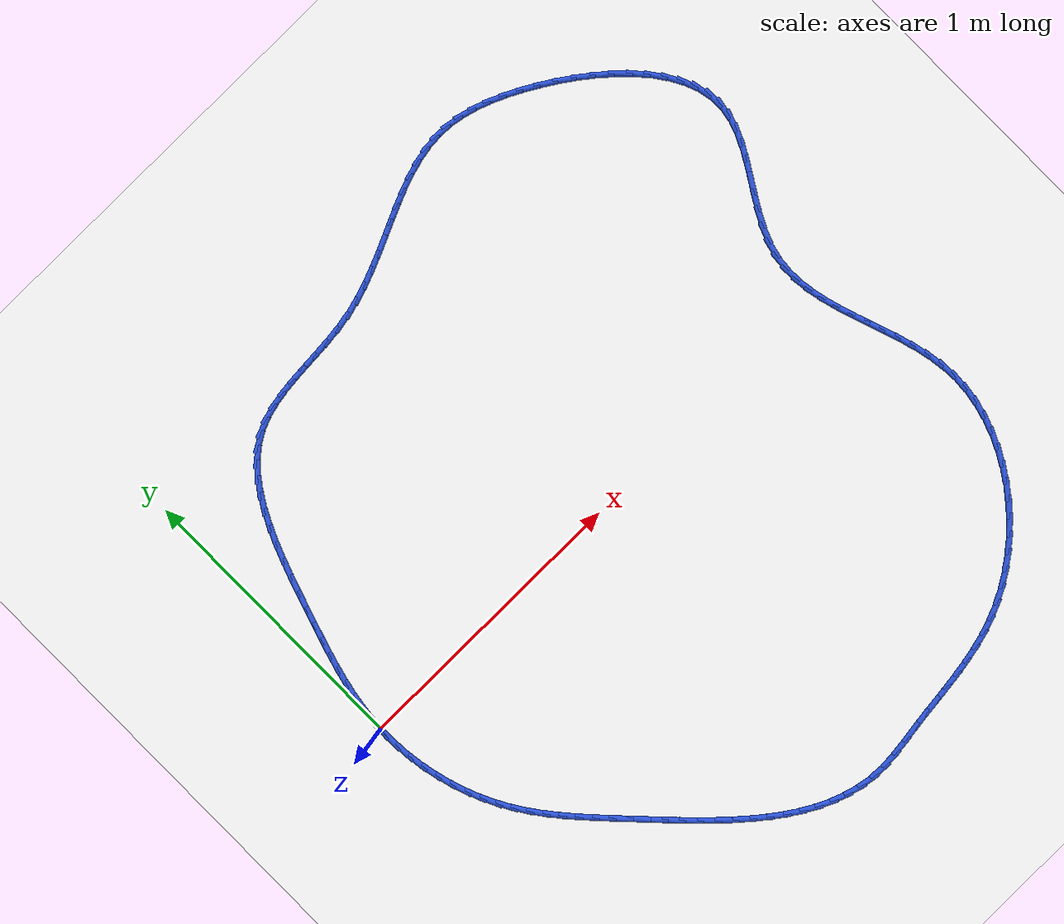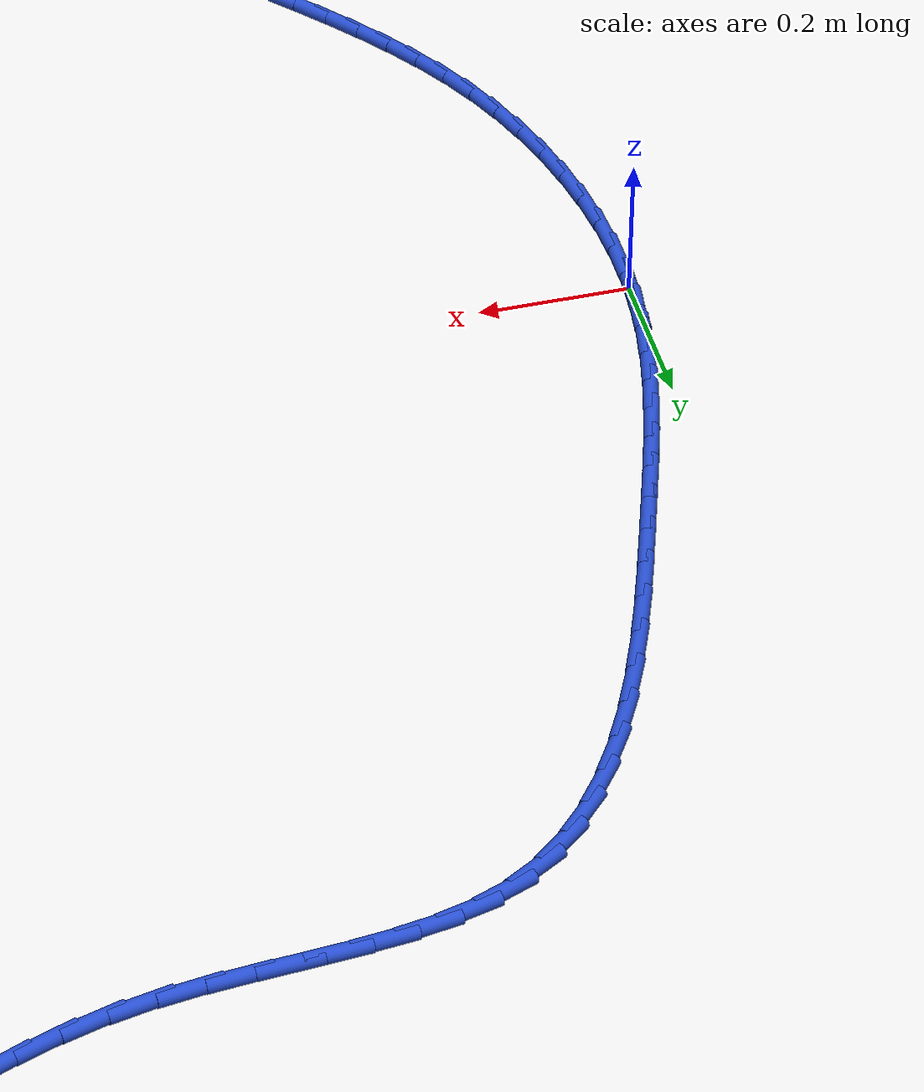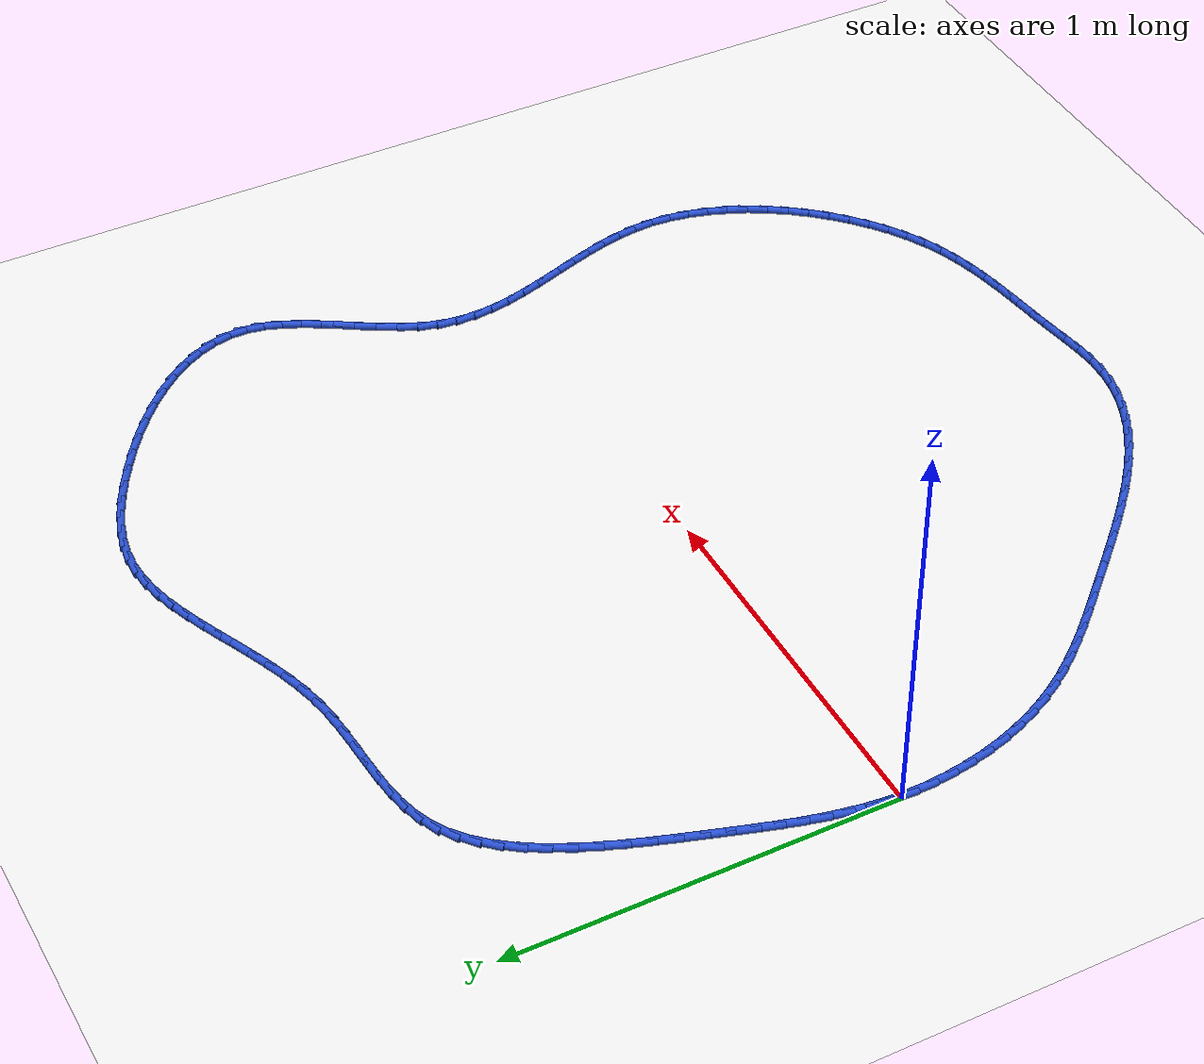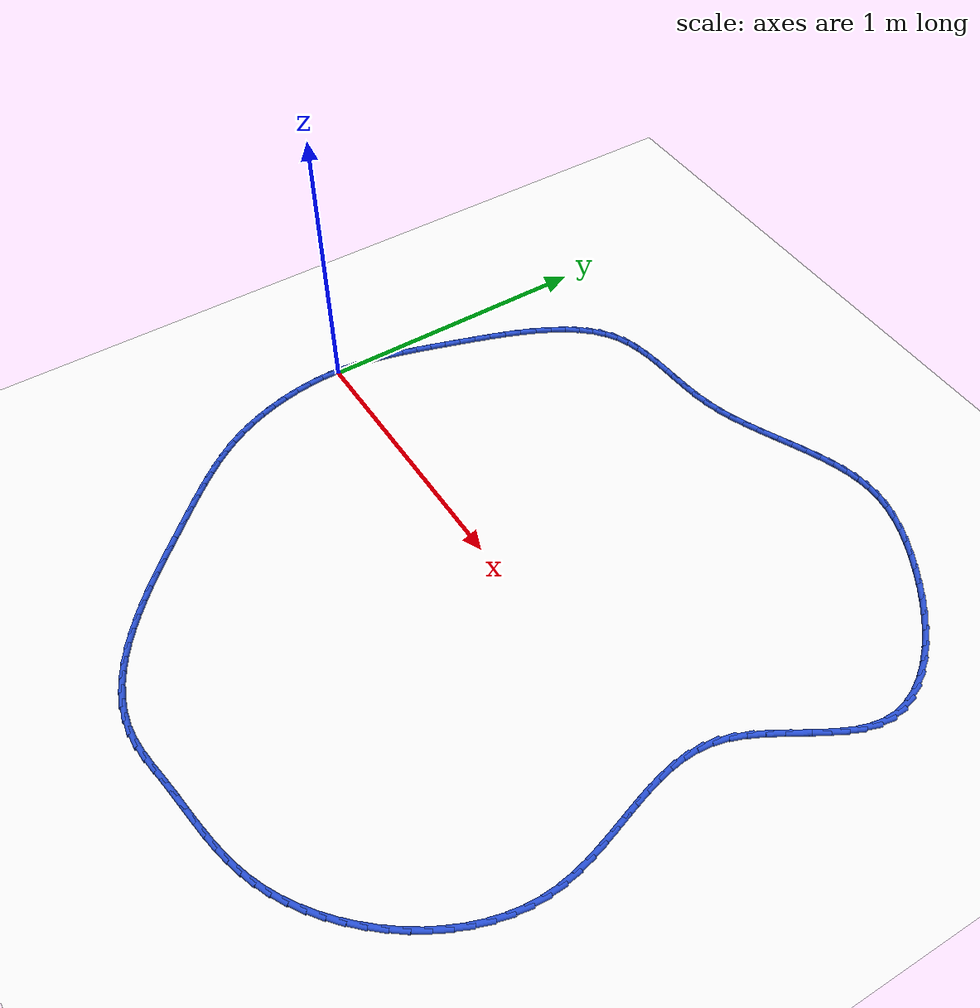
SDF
<sdf version="1.6">
 <world name="default">
  <light name="sun" type="directional">
   <pose>0 0 10 0 -0 0</pose>
   <diffuse>0.8 0.8 0.8 1</diffuse>
   <specular>0.2 0.2 0.2 1</specular>
   <attenuation>
    <range>1000</range>
    <constant>0.9</constant>
    <linear>0.01</linear>
    <quadratic>0.001</quadratic>
   </attenuation>
   <direction>-0.5 0.1 -0.9</direction>
  </light>
  <model name="ground_plane">
   <static>1</static>
   <link name="link">
    <collision name="collision">
     <geometry><plane><normal>0 0 1</normal><size>100 100</size></plane></geometry>
     <surface><friction><ode><mu>100</mu><mu2>50</mu2></ode></friction></surface>
    </collision>
    <visual name="visual">
     <cast_shadows>0</cast_shadows>
     <geometry><plane><normal>0 0 1</normal><size>100 100</size></plane></geometry>
     <material>
      <script><uri>file://media/materials/scripts/gazebo.material</uri><name>Gazebo/WhiteGlow</name></script>
     </material>
    </visual>
   </link>
  </model>
  <gravity>0 0 -9.8</gravity>
  <magnetic_field>6e-06 2.3e-05 -4.2e-05</magnetic_field>
  <atmosphere type="adiabatic"/>
  <physics name="default_physics" default="0" type="ode">
   <max_step_size>0.001</max_step_size>
   <real_time_factor>1</real_time_factor>
   <real_time_update_rate>1000</real_time_update_rate>
  </physics>
  <scene><ambient>0.4 0.4 0.4 1</ambient><background>0.7 0.7 0.7 1</background><shadows>1</shadows></scene>
  <spherical_coordinates>
   <surface_model>EARTH_WGS84</surface_model>
   <latitude_deg>0</latitude_deg>
   <longitude_deg>0</longitude_deg>
   <elevation>0</elevation>
   <heading_deg>0</heading_deg>
  </spherical_coordinates>
  <model name="line">
   <link name="link_0">
    <pose>2.42861286636753e-17 0.0 0.01 0 1.57 1.5062456968991784</pose>
    <collision name="collision">
     <geometry><cylinder><radius>0.01</radius><length>0.08</length></cylinder></geometry>
    </collision>
    <visual name="visual">
     <material>
      <script><name>Gazebo/Blue</name><uri>file://media/materials/scripts/gazebo.material</uri></script>
     </material>
     <geometry><cylinder><radius>0.01</radius><length>0.08</length></cylinder></geometry>
    </visual>
   </link>
   <link name="link_1">
    <pose>0.0033895039714401565 0.05243627973682007 0.01 0 1.57 1.4459991771651994</pose>
    <collision name="collision">
     <geometry><cylinder><radius>0.01</radius><length>0.08</length></cylinder></geometry>
    </collision>
    <visual name="visual">
     <material>
      <script><name>Gazebo/Blue</name><uri>file://media/materials/scripts/gazebo.material</uri></script>
     </material>
     <geometry><cylinder><radius>0.01</radius><length>0.08</length></cylinder></geometry>
    </visual>
   </link>
   <link name="link_2">
    <pose>0.009887980325377252 0.10423798213368149 0.01 0 1.57 1.3931108787442419</pose>
    <collision name="collision">
     <geometry><cylinder><radius>0.01</radius><length>0.08</length></cylinder></geometry>
    </collision>
    <visual name="visual">
     <material>
      <script><name>Gazebo/Blue</name><uri>file://media/materials/scripts/gazebo.material</uri></script>
     </material>
     <geometry><cylinder><radius>0.01</radius><length>0.08</length></cylinder></geometry>
    </visual>
   </link>
   <link name="link_3">
    <pose>0.019124163517237443 0.15567030890530242 0.01 0 1.57 1.3484846407170896</pose>
    <collision name="collision">
     <geometry><cylinder><radius>0.01</radius><length>0.08</length></cylinder></geometry>
    </collision>
    <visual name="visual">
     <material>
      <script><name>Gazebo/Blue</name><uri>file://media/materials/scripts/gazebo.material</uri></script>
     </material>
     <geometry><cylinder><radius>0.01</radius><length>0.08</length></cylinder></geometry>
    </visual>
   </link>
   <link name="link_4">
    <pose>0.03072678800244687 0.20699846176640097 0.01 0 1.57 1.312600667512587</pose>
    <collision name="collision">
     <geometry><cylinder><radius>0.01</radius><length>0.08</length></cylinder></geometry>
    </collision>
    <visual name="visual">
     <material>
      <script><name>Gazebo/Blue</name><uri>file://media/materials/scripts/gazebo.material</uri></script>
     </material>
     <geometry><cylinder><radius>0.01</radius><length>0.08</length></cylinder></geometry>
    </visual>
   </link>
   <link name="link_5">
    <pose>0.04432458823643169 0.2584876424316954 0.01 0 1.57 1.2855876910878032</pose>
    <collision name="collision">
     <geometry><cylinder><radius>0.01</radius><length>0.08</length></cylinder></geometry>
    </collision>
    <visual name="visual">
     <material>
      <script><name>Gazebo/Blue</name><uri>file://media/materials/scripts/gazebo.material</uri></script>
     </material>
     <geometry><cylinder><radius>0.01</radius><length>0.08</length></cylinder></geometry>
    </visual>
   </link>
   <link name="link_6">
    <pose>0.05954629867461807 0.31040305261590395 0.01 0 1.57 1.2673103484893582</pose>
    <collision name="collision">
     <geometry><cylinder><radius>0.01</radius><length>0.08</length></cylinder></geometry>
    </collision>
    <visual name="visual">
     <material>
      <script><name>Gazebo/Blue</name><uri>file://media/materials/scripts/gazebo.material</uri></script>
     </material>
     <geometry><cylinder><radius>0.01</radius><length>0.08</length></cylinder></geometry>
    </visual>
   </link>
   <link name="link_7">
    <pose>0.07602065377243208 0.36300989403374456 0.01 0 1.57 1.2574494163025367</pose>
    <collision name="collision">
     <geometry><cylinder><radius>0.01</radius><length>0.08</length></cylinder></geometry>
    </collision>
    <visual name="visual">
     <material>
      <script><name>Gazebo/Blue</name><uri>file://media/materials/scripts/gazebo.material</uri></script>
     </material>
     <geometry><cylinder><radius>0.01</radius><length>0.08</length></cylinder></geometry>
    </visual>
   </link>
   <link name="link_8">
    <pose>0.09337638798529999 0.41657336839993564 0.01 0 1.57 1.2546863573437124</pose>
    <collision name="collision">
     <geometry><cylinder><radius>0.01</radius><length>0.08</length></cylinder></geometry>
    </collision>
    <visual name="visual">
     <material>
      <script><name>Gazebo/Blue</name><uri>file://media/materials/scripts/gazebo.material</uri></script>
     </material>
     <geometry><cylinder><radius>0.01</radius><length>0.08</length></cylinder></geometry>
    </visual>
   </link>
   <link name="link_9">
    <pose>0.11127840652390608 0.4713065950076575 0.01 0 1.57 1.2490773098429868</pose>
    <collision name="collision">
     <geometry><cylinder><radius>0.01</radius><length>0.08</length></cylinder></geometry>
    </collision>
    <visual name="visual">
     <material>
      <script><name>Gazebo/Blue</name><uri>file://media/materials/scripts/gazebo.material</uri></script>
     </material>
     <geometry><cylinder><radius>0.01</radius><length>0.08</length></cylinder></geometry>
    </visual>
   </link>
   <link name="link_10">
    <pose>0.12979041490642082 0.5268484589220355 0.01 0 1.57 1.2347392475835262</pose>
    <collision name="collision">
     <geometry><cylinder><radius>0.01</radius><length>0.08</length></cylinder></geometry>
    </collision>
    <visual name="visual">
     <material>
      <script><name>Gazebo/Blue</name><uri>file://media/materials/scripts/gazebo.material</uri></script>
     </material>
     <geometry><cylinder><radius>0.01</radius><length>0.08</length></cylinder></geometry>
    </visual>
   </link>
   <link name="link_11">
    <pose>0.1492234732178619 0.5824816783344917 0.01 0 1.57 1.2113383774653015</pose>
    <collision name="collision">
     <geometry><cylinder><radius>0.01</radius><length>0.08</length></cylinder></geometry>
    </collision>
    <visual name="visual">
     <material>
      <script><name>Gazebo/Blue</name><uri>file://media/materials/scripts/gazebo.material</uri></script>
     </material>
     <geometry><cylinder><radius>0.01</radius><length>0.08</length></cylinder></geometry>
    </visual>
   </link>
   <link name="link_12">
    <pose>0.16989233986011076 0.6374836462145527 0.01 0 1.57 1.1781344930929152</pose>
    <collision name="collision">
     <geometry><cylinder><radius>0.01</radius><length>0.08</length></cylinder></geometry>
    </collision>
    <visual name="visual">
     <material>
      <script><name>Gazebo/Blue</name><uri>file://media/materials/scripts/gazebo.material</uri></script>
     </material>
     <geometry><cylinder><radius>0.01</radius><length>0.08</length></cylinder></geometry>
    </visual>
   </link>
   <link name="link_13">
    <pose>0.1921117732350489 0.6911317555317438 0.01 0 1.57 1.1338827301906536</pose>
    <collision name="collision">
     <geometry><cylinder><radius>0.01</radius><length>0.08</length></cylinder></geometry>
    </collision>
    <visual name="visual">
     <material>
      <script><name>Gazebo/Blue</name><uri>file://media/materials/scripts/gazebo.material</uri></script>
     </material>
     <geometry><cylinder><radius>0.01</radius><length>0.08</length></cylinder></geometry>
    </visual>
   </link>
   <link name="link_14">
    <pose>0.2161965317445578 0.7427033992555916 0.01 0 1.57 1.0768122276982357</pose>
    <collision name="collision">
     <geometry><cylinder><radius>0.01</radius><length>0.08</length></cylinder></geometry>
    </collision>
    <visual name="visual">
     <material>
      <script><name>Gazebo/Blue</name><uri>file://media/materials/scripts/gazebo.material</uri></script>
     </material>
     <geometry><cylinder><radius>0.01</radius><length>0.08</length></cylinder></geometry>
    </visual>
   </link>
   <link name="link_15">
    <pose>0.24246137379051907 0.7914759703556227 0.01 0 1.57 1.0046388859281228</pose>
    <collision name="collision">
     <geometry><cylinder><radius>0.01</radius><length>0.08</length></cylinder></geometry>
    </collision>
    <visual name="visual">
     <material>
      <script><name>Gazebo/Blue</name><uri>file://media/materials/scripts/gazebo.material</uri></script>
     </material>
     <geometry><cylinder><radius>0.01</radius><length>0.08</length></cylinder></geometry>
    </visual>
   </link>
   <link name="link_16">
    <pose>0.2712210577748142 0.8367268618013629 0.01 0 1.57 0.914706429832956</pose>
    <collision name="collision">
     <geometry><cylinder><radius>0.01</radius><length>0.08</length></cylinder></geometry>
    </collision>
    <visual name="visual">
     <material>
      <script><name>Gazebo/Blue</name><uri>file://media/materials/scripts/gazebo.material</uri></script>
     </material>
     <geometry><cylinder><radius>0.01</radius><length>0.08</length></cylinder></geometry>
    </visual>
   </link>
   <link name="link_17">
    <pose>0.3027903420993246 0.8777334665623385 0.01 0 1.57 0.8044260398442064</pose>
    <collision name="collision">
     <geometry><cylinder><radius>0.01</radius><length>0.08</length></cylinder></geometry>
    </collision>
    <visual name="visual">
     <material>
      <script><name>Gazebo/Blue</name><uri>file://media/materials/scripts/gazebo.material</uri></script>
     </material>
     <geometry><cylinder><radius>0.01</radius><length>0.08</length></cylinder></geometry>
    </visual>
   </link>
   <link name="link_18">
    <pose>0.3374839851659318 0.9137731776080759 0.01 0 1.57 0.6722414994403817</pose>
    <collision name="collision">
     <geometry><cylinder><radius>0.01</radius><length>0.08</length></cylinder></geometry>
    </collision>
    <visual name="visual">
     <material>
      <script><name>Gazebo/Blue</name><uri>file://media/materials/scripts/gazebo.material</uri></script>
     </material>
     <geometry><cylinder><radius>0.01</radius><length>0.08</length></cylinder></geometry>
    </visual>
   </link>
   <link name="link_19">
    <pose>0.37561674537651735 0.944123387908101 0.01 0 1.57 0.5192934539404767</pose>
    <collision name="collision">
     <geometry><cylinder><radius>0.01</radius><length>0.08</length></cylinder></geometry>
    </collision>
    <visual name="visual">
     <material>
      <script><name>Gazebo/Blue</name><uri>file://media/materials/scripts/gazebo.material</uri></script>
     </material>
     <geometry><cylinder><radius>0.01</radius><length>0.08</length></cylinder></geometry>
    </visual>
   </link>
   <link name="link_20">
    <pose>0.4175014910485277 0.9680657153807476 0.01 0 1.57 0.3645970820289732</pose>
    <collision name="collision">
     <geometry><cylinder><radius>0.01</radius><length>0.08</length></cylinder></geometry>
    </collision>
    <visual name="visual">
     <material>
      <script><name>Gazebo/Blue</name><uri>file://media/materials/scripts/gazebo.material</uri></script>
     </material>
     <geometry><cylinder><radius>0.01</radius><length>0.08</length></cylinder></geometry>
    </visual>
   </link>
   <link name="link_21">
    <pose>0.46317555225085694 0.98549769487003 0.01 0 1.57 0.24193190237719747</pose>
    <collision name="collision">
     <geometry><cylinder><radius>0.01</radius><length>0.08</length></cylinder></geometry>
    </collision>
    <visual name="visual">
     <material>
      <script><name>Gazebo/Blue</name><uri>file://media/materials/scripts/gazebo.material</uri></script>
     </material>
     <geometry><cylinder><radius>0.01</radius><length>0.08</length></cylinder></geometry>
    </visual>
   </link>
   <link name="link_22">
    <pose>0.5121138741070269 0.9975739731034287 0.01 0 1.57 0.15432786929534562</pose>
    <collision name="collision">
     <geometry><cylinder><radius>0.01</radius><length>0.08</length></cylinder></geometry>
    </collision>
    <visual name="visual">
     <material>
      <script><name>Gazebo/Blue</name><uri>file://media/materials/scripts/gazebo.material</uri></script>
     </material>
     <geometry><cylinder><radius>0.01</radius><length>0.08</length></cylinder></geometry>
    </visual>
   </link>
   <link name="link_23">
    <pose>0.5637228146156641 1.0056025111715954 0.01 0 1.57 0.09819612700172387</pose>
    <collision name="collision">
     <geometry><cylinder><radius>0.01</radius><length>0.08</length></cylinder></geometry>
    </collision>
    <visual name="visual">
     <material>
      <script><name>Gazebo/Blue</name><uri>file://media/materials/scripts/gazebo.material</uri></script>
     </material>
     <geometry><cylinder><radius>0.01</radius><length>0.08</length></cylinder></geometry>
    </visual>
   </link>
   <link name="link_24">
    <pose>0.6174087317753952 1.010891270165183 0.01 0 1.57 0.06979749722525311</pose>
    <collision name="collision">
     <geometry><cylinder><radius>0.01</radius><length>0.08</length></cylinder></geometry>
    </collision>
    <visual name="visual">
     <material>
      <script><name>Gazebo/Blue</name><uri>file://media/materials/scripts/gazebo.material</uri></script>
     </material>
     <geometry><cylinder><radius>0.01</radius><length>0.08</length></cylinder></geometry>
    </visual>
   </link>
   <link name="link_25">
    <pose>0.6725779835848471 1.014748211174844 0.01 0 1.57 0.0664939494357623</pose>
    <collision name="collision">
     <geometry><cylinder><radius>0.01</radius><length>0.08</length></cylinder></geometry>
    </collision>
    <visual name="visual">
     <material>
      <script><name>Gazebo/Blue</name><uri>file://media/materials/scripts/gazebo.material</uri></script>
     </material>
     <geometry><cylinder><radius>0.01</radius><length>0.08</length></cylinder></geometry>
    </visual>
   </link>
   <link name="link_26">
    <pose>0.7286369280426461 1.0184812952912305 0.01 0 1.57 0.08703339320356059</pose>
    <collision name="collision">
     <geometry><cylinder><radius>0.01</radius><length>0.08</length></cylinder></geometry>
    </collision>
    <visual name="visual">
     <material>
      <script><name>Gazebo/Blue</name><uri>file://media/materials/scripts/gazebo.material</uri></script>
     </material>
     <geometry><cylinder><radius>0.01</radius><length>0.08</length></cylinder></geometry>
    </visual>
   </link>
   <link name="link_27">
    <pose>0.7849919231474187 1.0233984836049954 0.01 0 1.57 0.1314109148363183</pose>
    <collision name="collision">
     <geometry><cylinder><radius>0.01</radius><length>0.08</length></cylinder></geometry>
    </collision>
    <visual name="visual">
     <material>
      <script><name>Gazebo/Blue</name><uri>file://media/materials/scripts/gazebo.material</uri></script>
     </material>
     <geometry><cylinder><radius>0.01</radius><length>0.08</length></cylinder></geometry>
    </visual>
   </link>
   <link name="link_28">
    <pose>0.8410493268977924 1.030807737206791 0.01 0 1.57 0.19980950240734566</pose>
    <collision name="collision">
     <geometry><cylinder><radius>0.01</radius><length>0.08</length></cylinder></geometry>
    </collision>
    <visual name="visual">
     <material>
      <script><name>Gazebo/Blue</name><uri>file://media/materials/scripts/gazebo.material</uri></script>
     </material>
     <geometry><cylinder><radius>0.01</radius><length>0.08</length></cylinder></geometry>
    </visual>
   </link>
   <link name="link_29">
    <pose>0.8962270902097718 1.0419818808376375 0.01 0 1.57 0.274602865221537</pose>
    <collision name="collision">
     <geometry><cylinder><radius>0.01</radius><length>0.08</length></cylinder></geometry>
    </collision>
    <visual name="visual">
     <material>
      <script><name>Gazebo/Blue</name><uri>file://media/materials/scripts/gazebo.material</uri></script>
     </material>
     <geometry><cylinder><radius>0.01</radius><length>0.08</length></cylinder></geometry>
    </visual>
   </link>
   <link name="link_30">
    <pose>0.9502688845117531 1.057206530459888 0.01 0 1.57 0.3351330704735034</pose>
    <collision name="collision">
     <geometry><cylinder><radius>0.01</radius><length>0.08</length></cylinder></geometry>
    </collision>
    <visual name="visual">
     <material>
      <script><name>Gazebo/Blue</name><uri>file://media/materials/scripts/gazebo.material</uri></script>
     </material>
     <geometry><cylinder><radius>0.01</radius><length>0.08</length></cylinder></geometry>
    </visual>
   </link>
   <link name="link_31">
    <pose>1.0032807583678407 1.075668992669595 0.01 0 1.57 0.38029731890670976</pose>
    <collision name="collision">
     <geometry><cylinder><radius>0.01</radius><length>0.08</length></cylinder></geometry>
    </collision>
    <visual name="visual">
     <material>
      <script><name>Gazebo/Blue</name><uri>file://media/materials/scripts/gazebo.material</uri></script>
     </material>
     <geometry><cylinder><radius>0.01</radius><length>0.08</length></cylinder></geometry>
    </visual>
   </link>
   <link name="link_32">
    <pose>1.0553877107324854 1.096499138344154 0.01 0 1.57 0.410317397783642</pose>
    <collision name="collision">
     <geometry><cylinder><radius>0.01</radius><length>0.08</length></cylinder></geometry>
    </collision>
    <visual name="visual">
     <material>
      <script><name>Gazebo/Blue</name><uri>file://media/materials/scripts/gazebo.material</uri></script>
     </material>
     <geometry><cylinder><radius>0.01</radius><length>0.08</length></cylinder></geometry>
    </visual>
   </link>
   <link name="link_33">
    <pose>1.1067147405601376 1.1188268383609614 0.01 0 1.57 0.4253567510582967</pose>
    <collision name="collision">
     <geometry><cylinder><radius>0.01</radius><length>0.08</length></cylinder></geometry>
    </collision>
    <visual name="visual">
     <material>
      <script><name>Gazebo/Blue</name><uri>file://media/materials/scripts/gazebo.material</uri></script>
     </material>
     <geometry><cylinder><radius>0.01</radius><length>0.08</length></cylinder></geometry>
    </visual>
   </link>
   <link name="link_34">
    <pose>1.1573868468052493 1.1417819635974125 0.01 0 1.57 0.42531304627636213</pose>
    <collision name="collision">
     <geometry><cylinder><radius>0.01</radius><length>0.08</length></cylinder></geometry>
    </collision>
    <visual name="visual">
     <material>
      <script><name>Gazebo/Blue</name><uri>file://media/materials/scripts/gazebo.material</uri></script>
     </material>
     <geometry><cylinder><radius>0.01</radius><length>0.08</length></cylinder></geometry>
    </visual>
   </link>
   <link name="link_35">
    <pose>1.207529028422271 1.1644943849309033 0.01 0 1.57 0.4096993636816247</pose>
    <collision name="collision">
     <geometry><cylinder><radius>0.01</radius><length>0.08</length></cylinder></geometry>
    </collision>
    <visual name="visual">
     <material>
      <script><name>Gazebo/Blue</name><uri>file://media/materials/scripts/gazebo.material</uri></script>
     </material>
     <geometry><cylinder><radius>0.01</radius><length>0.08</length></cylinder></geometry>
    </visual>
   </link>
   <link name="link_36">
    <pose>1.2572662843656537 1.18609397323883 0.01 0 1.57 0.37760422155665735</pose>
    <collision name="collision">
     <geometry><cylinder><radius>0.01</radius><length>0.08</length></cylinder></geometry>
    </collision>
    <visual name="visual">
     <material>
      <script><name>Gazebo/Blue</name><uri>file://media/materials/scripts/gazebo.material</uri></script>
     </material>
     <geometry><cylinder><radius>0.01</radius><length>0.08</length></cylinder></geometry>
    </visual>
   </link>
   <link name="link_37">
    <pose>1.3067236135898486 1.2057105993985886 0.01 0 1.57 0.32775156799154864</pose>
    <collision name="collision">
     <geometry><cylinder><radius>0.01</radius><length>0.08</length></cylinder></geometry>
    </collision>
    <visual name="visual">
     <material>
      <script><name>Gazebo/Blue</name><uri>file://media/materials/scripts/gazebo.material</uri></script>
     </material>
     <geometry><cylinder><radius>0.01</radius><length>0.08</length></cylinder></geometry>
    </visual>
   </link>
   <link name="link_38">
    <pose>1.3560260150493069 1.222474134287575 0.01 0 1.57 0.25872539393410193</pose>
    <collision name="collision">
     <geometry><cylinder><radius>0.01</radius><length>0.08</length></cylinder></geometry>
    </collision>
    <visual name="visual">
     <material>
      <script><name>Gazebo/Blue</name><uri>file://media/materials/scripts/gazebo.material</uri></script>
     </material>
     <geometry><cylinder><radius>0.01</radius><length>0.08</length></cylinder></geometry>
    </visual>
   </link>
   <link name="link_39">
    <pose>1.4052984876984786 1.2355144487831842 0.01 0 1.57 0.16946257647083465</pose>
    <collision name="collision">
     <geometry><cylinder><radius>0.01</radius><length>0.08</length></cylinder></geometry>
    </collision>
    <visual name="visual">
     <material>
      <script><name>Gazebo/Blue</name><uri>file://media/materials/scripts/gazebo.material</uri></script>
     </material>
     <geometry><cylinder><radius>0.01</radius><length>0.08</length></cylinder></geometry>
    </visual>
   </link>
   <link name="link_40">
    <pose>1.4546660304918162 1.2439614137628132 0.01 0 1.57 0.060093519521581526</pose>
    <collision name="collision">
     <geometry><cylinder><radius>0.01</radius><length>0.08</length></cylinder></geometry>
    </collision>
    <visual name="visual">
     <material>
      <script><name>Gazebo/Blue</name><uri>file://media/materials/scripts/gazebo.material</uri></script>
     </material>
     <geometry><cylinder><radius>0.01</radius><length>0.08</length></cylinder></geometry>
    </visual>
   </link>
   <link name="link_41">
    <pose>1.50425364238377 1.2469449001038577 0.01 0 1.57 -0.06376951316720172</pose>
    <collision name="collision">
     <geometry><cylinder><radius>0.01</radius><length>0.08</length></cylinder></geometry>
    </collision>
    <visual name="visual">
     <material>
      <script><name>Gazebo/Blue</name><uri>file://media/materials/scripts/gazebo.material</uri></script>
     </material>
     <geometry><cylinder><radius>0.01</radius><length>0.08</length></cylinder></geometry>
    </visual>
   </link>
   <link name="link_42">
    <pose>1.5541730609378048 1.2437572409872852 0.01 0 1.57 -0.17959205626005043</pose>
    <collision name="collision">
     <geometry><cylinder><radius>0.01</radius><length>0.08</length></cylinder></geometry>
    </collision>
    <visual name="visual">
     <material>
      <script><name>Gazebo/Blue</name><uri>file://media/materials/scripts/gazebo.material</uri></script>
     </material>
     <geometry><cylinder><radius>0.01</radius><length>0.08</length></cylinder></geometry>
    </visual>
   </link>
   <link name="link_43">
    <pose>1.6044595340750905 1.2346278269133066 0.01 0 1.57 -0.27888068944598643</pose>
    <collision name="collision">
     <geometry><cylinder><radius>0.01</radius><length>0.08</length></cylinder></geometry>
    </collision>
    <visual name="visual">
     <material>
      <script><name>Gazebo/Blue</name><uri>file://media/materials/scripts/gazebo.material</uri></script>
     </material>
     <geometry><cylinder><radius>0.01</radius><length>0.08</length></cylinder></geometry>
    </visual>
   </link>
   <link name="link_44">
    <pose>1.6551209444400943 1.220121294201809 0.01 0 1.57 -0.3618075823167382</pose>
    <collision name="collision">
     <geometry><cylinder><radius>0.01</radius><length>0.08</length></cylinder></geometry>
    </collision>
    <visual name="visual">
     <material>
      <script><name>Gazebo/Blue</name><uri>file://media/materials/scripts/gazebo.material</uri></script>
     </material>
     <geometry><cylinder><radius>0.01</radius><length>0.08</length></cylinder></geometry>
    </visual>
   </link>
   <link name="link_45">
    <pose>1.7061651401035685 1.2008027027274193 0.01 0 1.57 -0.4296223871402558</pose>
    <collision name="collision">
     <geometry><cylinder><radius>0.01</radius><length>0.08</length></cylinder></geometry>
    </collision>
    <visual name="visual">
     <material>
      <script><name>Gazebo/Blue</name><uri>file://media/materials/scripts/gazebo.material</uri></script>
     </material>
     <geometry><cylinder><radius>0.01</radius><length>0.08</length></cylinder></geometry>
    </visual>
   </link>
   <link name="link_46">
    <pose>1.7575999691362678 1.1772371123647654 0.01 0 1.57 -0.4839768215693797</pose>
    <collision name="collision">
     <geometry><cylinder><radius>0.01</radius><length>0.08</length></cylinder></geometry>
    </collision>
    <visual name="visual">
     <material>
      <script><name>Gazebo/Blue</name><uri>file://media/materials/scripts/gazebo.material</uri></script>
     </material>
     <geometry><cylinder><radius>0.01</radius><length>0.08</length></cylinder></geometry>
    </visual>
   </link>
   <link name="link_47">
    <pose>1.809433279608945 1.1499895829884748 0.01 0 1.57 -0.528381747543479</pose>
    <collision name="collision">
     <geometry><cylinder><radius>0.01</radius><length>0.08</length></cylinder></geometry>
    </collision>
    <visual name="visual">
     <material>
      <script><name>Gazebo/Blue</name><uri>file://media/materials/scripts/gazebo.material</uri></script>
     </material>
     <geometry><cylinder><radius>0.01</radius><length>0.08</length></cylinder></geometry>
    </visual>
   </link>
   <link name="link_48">
    <pose>1.8615339503997963 1.119576062675035 0.01 0 1.57 -0.5721277697215879</pose>
    <collision name="collision">
     <geometry><cylinder><radius>0.01</radius><length>0.08</length></cylinder></geometry>
    </collision>
    <visual name="visual">
     <material>
      <script><name>Gazebo/Blue</name><uri>file://media/materials/scripts/gazebo.material</uri></script>
     </material>
     <geometry><cylinder><radius>0.01</radius><length>0.08</length></cylinder></geometry>
    </visual>
   </link>
   <link name="link_49">
    <pose>1.91319366532953 1.0863085184125463 0.01 0 1.57 -0.6188107056609943</pose>
    <collision name="collision">
     <geometry><cylinder><radius>0.01</radius><length>0.08</length></cylinder></geometry>
    </collision>
    <visual name="visual">
     <material>
      <script><name>Gazebo/Blue</name><uri>file://media/materials/scripts/gazebo.material</uri></script>
     </material>
     <geometry><cylinder><radius>0.01</radius><length>0.08</length></cylinder></geometry>
    </visual>
   </link>
   <link name="link_50">
    <pose>1.9635542770698824 1.0504459667688884 0.01 0 1.57 -0.670117612487911</pose>
    <collision name="collision">
     <geometry><cylinder><radius>0.01</radius><length>0.08</length></cylinder></geometry>
    </collision>
    <visual name="visual">
     <material>
      <script><name>Gazebo/Blue</name><uri>file://media/materials/scripts/gazebo.material</uri></script>
     </material>
     <geometry><cylinder><radius>0.01</radius><length>0.08</length></cylinder></geometry>
    </visual>
   </link>
   <link name="link_51">
    <pose>2.0117576380077455 1.0122474242112784 0.01 0 1.57 -0.727981286906242</pose>
    <collision name="collision">
     <geometry><cylinder><radius>0.01</radius><length>0.08</length></cylinder></geometry>
    </collision>
    <visual name="visual">
     <material>
      <script><name>Gazebo/Blue</name><uri>file://media/materials/scripts/gazebo.material</uri></script>
     </material>
     <geometry><cylinder><radius>0.01</radius><length>0.08</length></cylinder></geometry>
    </visual>
   </link>
   <link name="link_52">
    <pose>2.056945600530009 0.9719719072069326 0.01 0 1.57 -0.7947382368862548</pose>
    <collision name="collision">
     <geometry><cylinder><radius>0.01</radius><length>0.08</length></cylinder></geometry>
    </collision>
    <visual name="visual">
     <material>
      <script><name>Gazebo/Blue</name><uri>file://media/materials/scripts/gazebo.material</uri></script>
     </material>
     <geometry><cylinder><radius>0.01</radius><length>0.08</length></cylinder></geometry>
    </visual>
   </link>
   <link name="link_53">
    <pose>2.098260017023563 0.9298784322230669 0.01 0 1.57 -0.8732833800559324</pose>
    <collision name="collision">
     <geometry><cylinder><radius>0.01</radius><length>0.08</length></cylinder></geometry>
    </collision>
    <visual name="visual">
     <material>
      <script><name>Gazebo/Blue</name><uri>file://media/materials/scripts/gazebo.material</uri></script>
     </material>
     <geometry><cylinder><radius>0.01</radius><length>0.08</length></cylinder></geometry>
    </visual>
   </link>
   <link name="link_54">
    <pose>2.1348427398753014 0.8862260157268989 0.01 0 1.57 -0.9671786636533485</pose>
    <collision name="collision">
     <geometry><cylinder><radius>0.01</radius><length>0.08</length></cylinder></geometry>
    </collision>
    <visual name="visual">
     <material>
      <script><name>Gazebo/Blue</name><uri>file://media/materials/scripts/gazebo.material</uri></script>
     </material>
     <geometry><cylinder><radius>0.01</radius><length>0.08</length></cylinder></geometry>
    </visual>
   </link>
   <link name="link_55">
    <pose>2.1658356214721133 0.8412736741856432 0.01 0 1.57 -1.0805824273977227</pose>
    <collision name="collision">
     <geometry><cylinder><radius>0.01</radius><length>0.08</length></cylinder></geometry>
    </collision>
    <visual name="visual">
     <material>
      <script><name>Gazebo/Blue</name><uri>file://media/materials/scripts/gazebo.material</uri></script>
     </material>
     <geometry><cylinder><radius>0.01</radius><length>0.08</length></cylinder></geometry>
    </visual>
   </link>
   <link name="link_56">
    <pose>2.1903805142008905 0.7952804240665182 0.01 0 1.57 -1.2176965936084658</pose>
    <collision name="collision">
     <geometry><cylinder><radius>0.01</radius><length>0.08</length></cylinder></geometry>
    </collision>
    <visual name="visual">
     <material>
      <script><name>Gazebo/Blue</name><uri>file://media/materials/scripts/gazebo.material</uri></script>
     </material>
     <geometry><cylinder><radius>0.01</radius><length>0.08</length></cylinder></geometry>
    </visual>
   </link>
   <link name="link_57">
    <pose>2.2076192704485234 0.7485052818367388 0.01 0 1.57 -1.3812423611241642</pose>
    <collision name="collision">
     <geometry><cylinder><radius>0.01</radius><length>0.08</length></cylinder></geometry>
    </collision>
    <visual name="visual">
     <material>
      <script><name>Gazebo/Blue</name><uri>file://media/materials/scripts/gazebo.material</uri></script>
     </material>
     <geometry><cylinder><radius>0.01</radius><length>0.08</length></cylinder></geometry>
    </visual>
   </link>
   <link name="link_58">
    <pose>2.2166937426019038 0.7012072639635223 0.01 0 1.57 -1.5697021642328135</pose>
    <collision name="collision">
     <geometry><cylinder><radius>0.01</radius><length>0.08</length></cylinder></geometry>
    </collision>
    <visual name="visual">
     <material>
      <script><name>Gazebo/Blue</name><uri>file://media/materials/scripts/gazebo.material</uri></script>
     </material>
     <geometry><cylinder><radius>0.01</radius><length>0.08</length></cylinder></geometry>
    </visual>
   </link>
   <link name="link_59">
    <pose>2.216745783047921 0.6536453869140842 0.01 0 1.57 1.3765695246528835</pose>
    <collision name="collision">
     <geometry><cylinder><radius>0.01</radius><length>0.08</length></cylinder></geometry>
    </collision>
    <visual name="visual">
     <material>
      <script><name>Gazebo/Blue</name><uri>file://media/materials/scripts/gazebo.material</uri></script>
     </material>
     <geometry><cylinder><radius>0.01</radius><length>0.08</length></cylinder></geometry>
    </visual>
   </link>
   <link name="link_60">
    <pose>2.207378923476059 0.6060269486554369 0.01 0 1.57 1.2223561097141546</pose>
    <collision name="collision">
     <geometry><cylinder><radius>0.01</radius><length>0.08</length></cylinder></geometry>
    </collision>
    <visual name="visual">
     <material>
      <script><name>Gazebo/Blue</name><uri>file://media/materials/scripts/gazebo.material</uri></script>
     </material>
     <geometry><cylinder><radius>0.01</radius><length>0.08</length></cylinder></geometry>
    </visual>
   </link>
   <link name="link_61">
    <pose>2.1900598966775893 0.5583505265859571 0.01 0 1.57 1.1165627376637237</pose>
    <collision name="collision">
     <geometry><cylinder><radius>0.01</radius><length>0.08</length></cylinder></geometry>
    </collision>
    <visual name="visual">
     <material>
      <script><name>Gazebo/Blue</name><uri>file://media/materials/scripts/gazebo.material</uri></script>
     </material>
     <geometry><cylinder><radius>0.01</radius><length>0.08</length></cylinder></geometry>
    </visual>
   </link>
   <link name="link_62">
    <pose>2.166725393409376 0.5105620522067429 0.01 0 1.57 1.0514826039585043</pose>
    <collision name="collision">
     <geometry><cylinder><radius>0.01</radius><length>0.08</length></cylinder></geometry>
    </collision>
    <visual name="visual">
     <material>
      <script><name>Gazebo/Blue</name><uri>file://media/materials/scripts/gazebo.material</uri></script>
     </material>
     <geometry><cylinder><radius>0.01</radius><length>0.08</length></cylinder></geometry>
    </visual>
   </link>
   <link name="link_63">
    <pose>2.1393121044403904 0.4626074570175358 0.01 0 1.57 1.0205071304001756</pose>
    <collision name="collision">
     <geometry><cylinder><radius>0.01</radius><length>0.08</length></cylinder></geometry>
    </collision>
    <visual name="visual">
     <material>
      <script><name>Gazebo/Blue</name><uri>file://media/materials/scripts/gazebo.material</uri></script>
     </material>
     <geometry><cylinder><radius>0.01</radius><length>0.08</length></cylinder></geometry>
    </visual>
   </link>
   <link name="link_64">
    <pose>2.109756720539605 0.41443267251807897 0.01 0 1.57 1.0199502787090715</pose>
    <collision name="collision">
     <geometry><cylinder><radius>0.01</radius><length>0.08</length></cylinder></geometry>
    </collision>
    <visual name="visual">
     <material>
      <script><name>Gazebo/Blue</name><uri>file://media/materials/scripts/gazebo.material</uri></script>
     </material>
     <geometry><cylinder><radius>0.01</radius><length>0.08</length></cylinder></geometry>
    </visual>
   </link>
   <link name="link_65">
    <pose>2.079995932475991 0.3659836302081138 0.01 0 1.57 1.0492314926855069</pose>
    <collision name="collision">
     <geometry><cylinder><radius>0.01</radius><length>0.08</length></cylinder></geometry>
    </collision>
    <visual name="visual">
     <material>
      <script><name>Gazebo/Blue</name><uri>file://media/materials/scripts/gazebo.material</uri></script>
     </material>
     <geometry><cylinder><radius>0.01</radius><length>0.08</length></cylinder></geometry>
    </visual>
   </link>
   <link name="link_66">
    <pose>2.0519664310185197 0.31720626158738197 0.01 0 1.57 1.1107084641364842</pose>
    <collision name="collision">
     <geometry><cylinder><radius>0.01</radius><length>0.08</length></cylinder></geometry>
    </collision>
    <visual name="visual">
     <material>
      <script><name>Gazebo/Blue</name><uri>file://media/materials/scripts/gazebo.material</uri></script>
     </material>
     <geometry><cylinder><radius>0.01</radius><length>0.08</length></cylinder></geometry>
    </visual>
   </link>
   <link name="link_67">
    <pose>2.0276049069361632 0.2680464981556266 0.01 0 1.57 1.2092308416880622</pose>
    <collision name="collision">
     <geometry><cylinder><radius>0.01</radius><length>0.08</length></cylinder></geometry>
    </collision>
    <visual name="visual">
     <material>
      <script><name>Gazebo/Blue</name><uri>file://media/materials/scripts/gazebo.material</uri></script>
     </material>
     <geometry><cylinder><radius>0.01</radius><length>0.08</length></cylinder></geometry>
    </visual>
   </link>
   <link name="link_68">
    <pose>2.008848050997894 0.21845027141258871 0.01 0 1.57 1.3478094952100241</pose>
    <collision name="collision">
     <geometry><cylinder><radius>0.01</radius><length>0.08</length></cylinder></geometry>
    </collision>
    <visual name="visual">
     <material>
      <script><name>Gazebo/Blue</name><uri>file://media/materials/scripts/gazebo.material</uri></script>
     </material>
     <geometry><cylinder><radius>0.01</radius><length>0.08</length></cylinder></geometry>
    </visual>
   </link>
   <link name="link_69">
    <pose>1.9974913631397733 0.1683673546811499 0.01 0 1.57 1.494268745782904</pose>
    <collision name="collision">
     <geometry><cylinder><radius>0.01</radius><length>0.08</length></cylinder></geometry>
    </collision>
    <visual name="visual">
     <material>
      <script><name>Gazebo/Blue</name><uri>file://media/materials/scripts/gazebo.material</uri></script>
     </material>
     <geometry><cylinder><radius>0.01</radius><length>0.08</length></cylinder></geometry>
    </visual>
   </link>
   <link name="link_70">
    <pose>1.9936135516059965 0.11779423543630574 0.01 0 1.57 -1.5211610270993388</pose>
    <collision name="collision">
     <geometry><cylinder><radius>0.01</radius><length>0.08</length></cylinder></geometry>
    </collision>
    <visual name="visual">
     <material>
      <script><name>Gazebo/Blue</name><uri>file://media/materials/scripts/gazebo.material</uri></script>
     </material>
     <geometry><cylinder><radius>0.01</radius><length>0.08</length></cylinder></geometry>
    </visual>
   </link>
   <link name="link_71">
    <pose>1.996148805807633 0.06675854367728853 0.01 0 1.57 -1.419224589580382</pose>
    <collision name="collision">
     <geometry><cylinder><radius>0.01</radius><length>0.08</length></cylinder></geometry>
    </collision>
    <visual name="visual">
     <material>
      <script><name>Gazebo/Blue</name><uri>file://media/materials/scripts/gazebo.material</uri></script>
     </material>
     <geometry><cylinder><radius>0.01</radius><length>0.08</length></cylinder></geometry>
    </visual>
   </link>
   <link name="link_72">
    <pose>2.0040105107833446 0.015288475493334236 0.01 0 1.57 -1.3416177244611234</pose>
    <collision name="collision">
     <geometry><cylinder><radius>0.01</radius><length>0.08</length></cylinder></geometry>
    </collision>
    <visual name="visual">
     <material>
      <script><name>Gazebo/Blue</name><uri>file://media/materials/scripts/gazebo.material</uri></script>
     </material>
     <geometry><cylinder><radius>0.01</radius><length>0.08</length></cylinder></geometry>
    </visual>
   </link>
   <link name="link_73">
    <pose>2.016112051571794 -0.03658777302632177 0.01 0 1.57 -1.2867563114248148</pose>
    <collision name="collision">
     <geometry><cylinder><radius>0.01</radius><length>0.08</length></cylinder></geometry>
    </collision>
    <visual name="visual">
     <material>
      <script><name>Gazebo/Blue</name><uri>file://media/materials/scripts/gazebo.material</uri></script>
     </material>
     <geometry><cylinder><radius>0.01</radius><length>0.08</length></cylinder></geometry>
    </visual>
   </link>
   <link name="link_74">
    <pose>2.031366813211641 -0.08884200579244145 0.01 0 1.57 -1.252699646388601</pose>
    <collision name="collision">
     <geometry><cylinder><radius>0.01</radius><length>0.08</length></cylinder></geometry>
    </collision>
    <visual name="visual">
     <material>
      <script><name>Gazebo/Blue</name><uri>file://media/materials/scripts/gazebo.material</uri></script>
     </material>
     <geometry><cylinder><radius>0.01</radius><length>0.08</length></cylinder></geometry>
    </visual>
   </link>
   <link name="link_75">
    <pose>2.0486881807415496 -0.1414460267157893 0.01 0 1.57 -1.2378734197632872</pose>
    <collision name="collision">
     <geometry><cylinder><radius>0.01</radius><length>0.08</length></cylinder></geometry>
    </collision>
    <visual name="visual">
     <material>
      <script><name>Gazebo/Blue</name><uri>file://media/materials/scripts/gazebo.material</uri></script>
     </material>
     <geometry><cylinder><radius>0.01</radius><length>0.08</length></cylinder></geometry>
    </visual>
   </link>
   <link name="link_76">
    <pose>2.066989539200182 -0.194371639707129 0.01 0 1.57 -1.2413698996060933</pose>
    <collision name="collision">
     <geometry><cylinder><radius>0.01</radius><length>0.08</length></cylinder></geometry>
    </collision>
    <visual name="visual">
     <material>
      <script><name>Gazebo/Blue</name><uri>file://media/materials/scripts/gazebo.material</uri></script>
     </material>
     <geometry><cylinder><radius>0.01</radius><length>0.08</length></cylinder></geometry>
    </visual>
   </link>
   <link name="link_77">
    <pose>2.085184273626199 -0.24759064867722425 0.01 0 1.57 -1.263018742705472</pose>
    <collision name="collision">
     <geometry><cylinder><radius>0.01</radius><length>0.08</length></cylinder></geometry>
    </collision>
    <visual name="visual">
     <material>
      <script><name>Gazebo/Blue</name><uri>file://media/materials/scripts/gazebo.material</uri></script>
     </material>
     <geometry><cylinder><radius>0.01</radius><length>0.08</length></cylinder></geometry>
    </visual>
   </link>
   <link name="link_78">
    <pose>2.102185769058264 -0.3010748575368397 0.01 0 1.57 -1.3033249106179878</pose>
    <collision name="collision">
     <geometry><cylinder><radius>0.01</radius><length>0.08</length></cylinder></geometry>
    </collision>
    <visual name="visual">
     <material>
      <script><name>Gazebo/Blue</name><uri>file://media/materials/scripts/gazebo.material</uri></script>
     </material>
     <geometry><cylinder><radius>0.01</radius><length>0.08</length></cylinder></geometry>
    </visual>
   </link>
   <link name="link_79">
    <pose>2.116907410535038 -0.3547960701967372 0.01 0 1.57 -1.3632737501175733</pose>
    <collision name="collision">
     <geometry><cylinder><radius>0.01</radius><length>0.08</length></cylinder></geometry>
    </collision>
    <visual name="visual">
     <material>
      <script><name>Gazebo/Blue</name><uri>file://media/materials/scripts/gazebo.material</uri></script>
     </material>
     <geometry><cylinder><radius>0.01</radius><length>0.08</length></cylinder></geometry>
    </visual>
   </link>
   <link name="link_80">
    <pose>2.128262583095183 -0.4087260905676813 0.01 0 1.57 -1.4439263084551768</pose>
    <collision name="collision">
     <geometry><cylinder><radius>0.01</radius><length>0.08</length></cylinder></geometry>
    </collision>
    <visual name="visual">
     <material>
      <script><name>Gazebo/Blue</name><uri>file://media/materials/scripts/gazebo.material</uri></script>
     </material>
     <geometry><cylinder><radius>0.01</radius><length>0.08</length></cylinder></geometry>
    </visual>
   </link>
   <link name="link_81">
    <pose>2.135164671777362 -0.4628367225604355 0.01 0 1.57 -1.5452894200503906</pose>
    <collision name="collision">
     <geometry><cylinder><radius>0.01</radius><length>0.08</length></cylinder></geometry>
    </collision>
    <visual name="visual">
     <material>
      <script><name>Gazebo/Blue</name><uri>file://media/materials/scripts/gazebo.material</uri></script>
     </material>
     <geometry><cylinder><radius>0.01</radius><length>0.08</length></cylinder></geometry>
    </visual>
   </link>
   <link name="link_82">
    <pose>2.1365489396836734 -0.5170952692563825 0.01 0 1.57 1.4870841949405584</pose>
    <collision name="collision">
     <geometry><cylinder><radius>0.01</radius><length>0.08</length></cylinder></geometry>
    </collision>
    <visual name="visual">
     <material>
      <script><name>Gazebo/Blue</name><uri>file://media/materials/scripts/gazebo.material</uri></script>
     </material>
     <geometry><cylinder><radius>0.01</radius><length>0.08</length></cylinder></geometry>
    </visual>
   </link>
   <link name="link_83">
    <pose>2.13199770295842 -0.5713359197913909 0.01 0 1.57 1.384400701026901</pose>
    <collision name="collision">
     <geometry><cylinder><radius>0.01</radius><length>0.08</length></cylinder></geometry>
    </collision>
    <visual name="visual">
     <material>
      <script><name>Gazebo/Blue</name><uri>file://media/materials/scripts/gazebo.material</uri></script>
     </material>
     <geometry><cylinder><radius>0.01</radius><length>0.08</length></cylinder></geometry>
    </visual>
   </link>
   <link name="link_84">
    <pose>2.1218320509750916 -0.6252408803680027 0.01 0 1.57 1.2889178028825368</pose>
    <collision name="collision">
     <geometry><cylinder><radius>0.01</radius><length>0.08</length></cylinder></geometry>
    </collision>
    <visual name="visual">
     <material>
      <script><name>Gazebo/Blue</name><uri>file://media/materials/scripts/gazebo.material</uri></script>
     </material>
     <geometry><cylinder><radius>0.01</radius><length>0.08</length></cylinder></geometry>
    </visual>
   </link>
   <link name="link_85">
    <pose>2.1064133963194 -0.6784840617608336 0.01 0 1.57 1.200092322463749</pose>
    <collision name="collision">
     <geometry><cylinder><radius>0.01</radius><length>0.08</length></cylinder></geometry>
    </collision>
    <visual name="visual">
     <material>
      <script><name>Gazebo/Blue</name><uri>file://media/materials/scripts/gazebo.material</uri></script>
     </material>
     <geometry><cylinder><radius>0.01</radius><length>0.08</length></cylinder></geometry>
    </visual>
   </link>
   <link name="link_86">
    <pose>2.0861031515770594 -0.7307393747445 0.01 0 1.57 1.1170953570794266</pose>
    <collision name="collision">
     <geometry><cylinder><radius>0.01</radius><length>0.08</length></cylinder></geometry>
    </collision>
    <visual name="visual">
     <material>
      <script><name>Gazebo/Blue</name><uri>file://media/materials/scripts/gazebo.material</uri></script>
     </material>
     <geometry><cylinder><radius>0.01</radius><length>0.08</length></cylinder></geometry>
    </visual>
   </link>
   <link name="link_87">
    <pose>2.0612627293337824 -0.7816807300936185 0.01 0 1.57 1.0389454247448633</pose>
    <collision name="collision">
     <geometry><cylinder><radius>0.01</radius><length>0.08</length></cylinder></geometry>
    </collision>
    <visual name="visual">
     <material>
      <script><name>Gazebo/Blue</name><uri>file://media/materials/scripts/gazebo.material</uri></script>
     </material>
     <geometry><cylinder><radius>0.01</radius><length>0.08</length></cylinder></geometry>
    </visual>
   </link>
   <link name="link_88">
    <pose>2.032253542175284 -0.8309820385828038 0.01 0 1.57 0.9645945229496923</pose>
    <collision name="collision">
     <geometry><cylinder><radius>0.01</radius><length>0.08</length></cylinder></geometry>
    </collision>
    <visual name="visual">
     <material>
      <script><name>Gazebo/Blue</name><uri>file://media/materials/scripts/gazebo.material</uri></script>
     </material>
     <geometry><cylinder><radius>0.01</radius><length>0.08</length></cylinder></geometry>
    </visual>
   </link>
   <link name="link_89">
    <pose>1.999437002687277 -0.8783172109866724 0.01 0 1.57 0.8929748739932691</pose>
    <collision name="collision">
     <geometry><cylinder><radius>0.01</radius><length>0.08</length></cylinder></geometry>
    </collision>
    <visual name="visual">
     <material>
      <script><name>Gazebo/Blue</name><uri>file://media/materials/scripts/gazebo.material</uri></script>
     </material>
     <geometry><cylinder><radius>0.01</radius><length>0.08</length></cylinder></geometry>
    </visual>
   </link>
   <link name="link_90">
    <pose>1.9631745234554752 -0.9233601580798406 0.01 0 1.57 0.8230172481504284</pose>
    <collision name="collision">
     <geometry><cylinder><radius>0.01</radius><length>0.08</length></cylinder></geometry>
    </collision>
    <visual name="visual">
     <material>
      <script><name>Gazebo/Blue</name><uri>file://media/materials/scripts/gazebo.material</uri></script>
     </material>
     <geometry><cylinder><radius>0.01</radius><length>0.08</length></cylinder></geometry>
    </visual>
   </link>
   <link name="link_91">
    <pose>1.9238275170655914 -0.9657847906369251 0.01 0 1.57 0.7536506357209586</pose>
    <collision name="collision">
     <geometry><cylinder><radius>0.01</radius><length>0.08</length></cylinder></geometry>
    </collision>
    <visual name="visual">
     <material>
      <script><name>Gazebo/Blue</name><uri>file://media/materials/scripts/gazebo.material</uri></script>
     </material>
     <geometry><cylinder><radius>0.01</radius><length>0.08</length></cylinder></geometry>
    </visual>
   </link>
   <link name="link_92">
    <pose>1.88175739610334 -1.0052650194325408 0.01 0 1.57 0.6837908445344936</pose>
    <collision name="collision">
     <geometry><cylinder><radius>0.01</radius><length>0.08</length></cylinder></geometry>
    </collision>
    <visual name="visual">
     <material>
      <script><name>Gazebo/Blue</name><uri>file://media/materials/scripts/gazebo.material</uri></script>
     </material>
     <geometry><cylinder><radius>0.01</radius><length>0.08</length></cylinder></geometry>
    </visual>
   </link>
   <link name="link_93">
    <pose>1.8373255731544351 -1.0414747552413042 0.01 0 1.57 0.6123238960724106</pose>
    <collision name="collision">
     <geometry><cylinder><radius>0.01</radius><length>0.08</length></cylinder></geometry>
    </collision>
    <visual name="visual">
     <material>
      <script><name>Gazebo/Blue</name><uri>file://media/materials/scripts/gazebo.material</uri></script>
     </material>
     <geometry><cylinder><radius>0.01</radius><length>0.08</length></cylinder></geometry>
    </visual>
   </link>
   <link name="link_94">
    <pose>1.7908934608045892 -1.0740879088378315 0.01 0 1.57 0.5380895559328759</pose>
    <collision name="collision">
     <geometry><cylinder><radius>0.01</radius><length>0.08</length></cylinder></geometry>
    </collision>
    <visual name="visual">
     <material>
      <script><name>Gazebo/Blue</name><uri>file://media/materials/scripts/gazebo.material</uri></script>
     </material>
     <geometry><cylinder><radius>0.01</radius><length>0.08</length></cylinder></geometry>
    </visual>
   </link>
   <link name="link_95">
    <pose>1.7428224716395149 -1.1027783909967388 0.01 0 1.57 0.45987131070319226</pose>
    <collision name="collision">
     <geometry><cylinder><radius>0.01</radius><length>0.08</length></cylinder></geometry>
    </collision>
    <visual name="visual">
     <material>
      <script><name>Gazebo/Blue</name><uri>file://media/materials/scripts/gazebo.material</uri></script>
     </material>
     <geometry><cylinder><radius>0.01</radius><length>0.08</length></cylinder></geometry>
    </visual>
   </link>
   <link name="link_96">
    <pose>1.6934740182449275 -1.1272201124926418 0.01 0 1.57 0.3780984687738225</pose>
    <collision name="collision">
     <geometry><cylinder><radius>0.01</radius><length>0.08</length></cylinder></geometry>
    </collision>
    <visual name="visual">
     <material>
      <script><name>Gazebo/Blue</name><uri>file://media/materials/scripts/gazebo.material</uri></script>
     </material>
     <geometry><cylinder><radius>0.01</radius><length>0.08</length></cylinder></geometry>
    </visual>
   </link>
   <link name="link_97">
    <pose>1.6431813503494275 -1.1471968383952635 0.01 0 1.57 0.3028963763006265</pose>
    <collision name="collision">
     <geometry><cylinder><radius>0.01</radius><length>0.08</length></cylinder></geometry>
    </collision>
    <visual name="visual">
     <material>
      <script><name>Gazebo/Blue</name><uri>file://media/materials/scripts/gazebo.material</uri></script>
     </material>
     <geometry><cylinder><radius>0.01</radius><length>0.08</length></cylinder></geometry>
    </visual>
   </link>
   <link name="link_98">
    <pose>1.592107008581118 -1.1631582153583193 0.01 0 1.57 0.23962322826591073</pose>
    <collision name="collision">
     <geometry><cylinder><radius>0.01</radius><length>0.08</length></cylinder></geometry>
    </collision>
    <visual name="visual">
     <material>
      <script><name>Gazebo/Blue</name><uri>file://media/materials/scripts/gazebo.material</uri></script>
     </material>
     <geometry><cylinder><radius>0.01</radius><length>0.08</length></cylinder></geometry>
    </visual>
   </link>
   <link name="link_99">
    <pose>1.5403495516875432 -1.1758034628810707 0.01 0 1.57 0.18930623276233927</pose>
    <collision name="collision">
     <geometry><cylinder><radius>0.01</radius><length>0.08</length></cylinder></geometry>
    </collision>
    <visual name="visual">
     <material>
      <script><name>Gazebo/Blue</name><uri>file://media/materials/scripts/gazebo.material</uri></script>
     </material>
     <geometry><cylinder><radius>0.01</radius><length>0.08</length></cylinder></geometry>
    </visual>
   </link>
   <link name="link_100">
    <pose>1.4880074255475104 -1.1858322407276072 0.01 0 1.57 0.1523632430268149</pose>
    <collision name="collision">
     <geometry><cylinder><radius>0.01</radius><length>0.08</length></cylinder></geometry>
    </collision>
    <visual name="visual">
     <material>
      <script><name>Gazebo/Blue</name><uri>file://media/materials/scripts/gazebo.material</uri></script>
     </material>
     <geometry><cylinder><radius>0.01</radius><length>0.08</length></cylinder></geometry>
    </visual>
   </link>
   <link name="link_101">
    <pose>1.4351790760398304 -1.19394420866202 0.01 0 1.57 0.12884481246914453</pose>
    <collision name="collision">
     <geometry><cylinder><radius>0.01</radius><length>0.08</length></cylinder></geometry>
    </collision>
    <visual name="visual">
     <material>
      <script><name>Gazebo/Blue</name><uri>file://media/materials/scripts/gazebo.material</uri></script>
     </material>
     <geometry><cylinder><radius>0.01</radius><length>0.08</length></cylinder></geometry>
    </visual>
   </link>
   <link name="link_102">
    <pose>1.3819629490433119 -1.200839026448399 0.01 0 1.57 0.11863056537637429</pose>
    <collision name="collision">
     <geometry><cylinder><radius>0.01</radius><length>0.08</length></cylinder></geometry>
    </collision>
    <visual name="visual">
     <material>
      <script><name>Gazebo/Blue</name><uri>file://media/materials/scripts/gazebo.material</uri></script>
     </material>
     <geometry><cylinder><radius>0.01</radius><length>0.08</length></cylinder></geometry>
    </visual>
   </link>
   <link name="link_103">
    <pose>1.3284574904367619 -1.207216353850834 0.01 0 1.57 0.12155682384455437</pose>
    <collision name="collision">
     <geometry><cylinder><radius>0.01</radius><length>0.08</length></cylinder></geometry>
    </collision>
    <visual name="visual">
     <material>
      <script><name>Gazebo/Blue</name><uri>file://media/materials/scripts/gazebo.material</uri></script>
     </material>
     <geometry><cylinder><radius>0.01</radius><length>0.08</length></cylinder></geometry>
    </visual>
   </link>
   <link name="link_104">
    <pose>1.2747611460989894 -1.2137758506334155 0.01 0 1.57 0.1369938170093388</pose>
    <collision name="collision">
     <geometry><cylinder><radius>0.01</radius><length>0.08</length></cylinder></geometry>
    </collision>
    <visual name="visual">
     <material>
      <script><name>Gazebo/Blue</name><uri>file://media/materials/scripts/gazebo.material</uri></script>
     </material>
     <geometry><cylinder><radius>0.01</radius><length>0.08</length></cylinder></geometry>
    </visual>
   </link>
   <link name="link_105">
    <pose>1.2209746849762713 -1.221190707011463 0.01 0 1.57 0.14374409153349707</pose>
    <collision name="collision">
     <geometry><cylinder><radius>0.01</radius><length>0.08</length></cylinder></geometry>
    </collision>
    <visual name="visual">
     <material>
      <script><name>Gazebo/Blue</name><uri>file://media/materials/scripts/gazebo.material</uri></script>
     </material>
     <geometry><cylinder><radius>0.01</radius><length>0.08</length></cylinder></geometry>
    </visual>
   </link>
   <link name="link_106">
    <pose>1.167301971257591 -1.2289594230142982 0.01 0 1.57 0.11237302761041162</pose>
    <collision name="collision">
     <geometry><cylinder><radius>0.01</radius><length>0.08</length></cylinder></geometry>
    </collision>
    <visual name="visual">
     <material>
      <script><name>Gazebo/Blue</name><uri>file://media/materials/scripts/gazebo.material</uri></script>
     </material>
     <geometry><cylinder><radius>0.01</radius><length>0.08</length></cylinder></geometry>
    </visual>
   </link>
   <link name="link_107">
    <pose>1.1140886990096381 -1.234964457416122 0.01 0 1.57 0.0382726738082082</pose>
    <collision name="collision">
     <geometry><cylinder><radius>0.01</radius><length>0.08</length></cylinder></geometry>
    </collision>
    <visual name="visual">
     <material>
      <script><name>Gazebo/Blue</name><uri>file://media/materials/scripts/gazebo.material</uri></script>
     </material>
     <geometry><cylinder><radius>0.01</radius><length>0.08</length></cylinder></geometry>
    </visual>
   </link>
   <link name="link_108">
    <pose>1.0616908598721115 -1.2369708425667247 0.01 0 1.57 -0.07167542441182356</pose>
    <collision name="collision">
     <geometry><cylinder><radius>0.01</radius><length>0.08</length></cylinder></geometry>
    </collision>
    <visual name="visual">
     <material>
      <script><name>Gazebo/Blue</name><uri>file://media/materials/scripts/gazebo.material</uri></script>
     </material>
     <geometry><cylinder><radius>0.01</radius><length>0.08</length></cylinder></geometry>
    </visual>
   </link>
   <link name="link_109">
    <pose>1.0103844755536808 -1.2332871253323094 0.01 0 1.57 -0.18296580059716036</pose>
    <collision name="collision">
     <geometry><cylinder><radius>0.01</radius><length>0.08</length></cylinder></geometry>
    </collision>
    <visual name="visual">
     <material>
      <script><name>Gazebo/Blue</name><uri>file://media/materials/scripts/gazebo.material</uri></script>
     </material>
     <geometry><cylinder><radius>0.01</radius><length>0.08</length></cylinder></geometry>
    </visual>
   </link>
   <link name="link_110">
    <pose>0.9601841896277209 -1.2239983054155605 0.01 0 1.57 -0.28597133093070265</pose>
    <collision name="collision">
     <geometry><cylinder><radius>0.01</radius><length>0.08</length></cylinder></geometry>
    </collision>
    <visual name="visual">
     <material>
      <script><name>Gazebo/Blue</name><uri>file://media/materials/scripts/gazebo.material</uri></script>
     </material>
     <geometry><cylinder><radius>0.01</radius><length>0.08</length></cylinder></geometry>
    </visual>
   </link>
   <link name="link_111">
    <pose>0.9110513301264971 -1.2095517408477188 0.01 0 1.57 -0.3789877202231385</pose>
    <collision name="collision">
     <geometry><cylinder><radius>0.01</radius><length>0.08</length></cylinder></geometry>
    </collision>
    <visual name="visual">
     <material>
      <script><name>Gazebo/Blue</name><uri>file://media/materials/scripts/gazebo.material</uri></script>
     </material>
     <geometry><cylinder><radius>0.01</radius><length>0.08</length></cylinder></geometry>
    </visual>
   </link>
   <link name="link_112">
    <pose>0.862947225082277 -1.1903947896600233 0.01 0 1.57 -0.46131809682366204</pose>
    <collision name="collision">
     <geometry><cylinder><radius>0.01</radius><length>0.08</length></cylinder></geometry>
    </collision>
    <visual name="visual">
     <material>
      <script><name>Gazebo/Blue</name><uri>file://media/materials/scripts/gazebo.material</uri></script>
     </material>
     <geometry><cylinder><radius>0.01</radius><length>0.08</length></cylinder></geometry>
    </visual>
   </link>
   <link name="link_113">
    <pose>0.8158332025273256 -1.1669748098837154 0.01 0 1.57 -0.5330294378595679</pose>
    <collision name="collision">
     <geometry><cylinder><radius>0.01</radius><length>0.08</length></cylinder></geometry>
    </collision>
    <visual name="visual">
     <material>
      <script><name>Gazebo/Blue</name><uri>file://media/materials/scripts/gazebo.material</uri></script>
     </material>
     <geometry><cylinder><radius>0.01</radius><length>0.08</length></cylinder></geometry>
    </visual>
   </link>
   <link name="link_114">
    <pose>0.7696705904939116 -1.1397391595500348 0.01 0 1.57 -0.5946645580351585</pose>
    <collision name="collision">
     <geometry><cylinder><radius>0.01</radius><length>0.08</length></cylinder></geometry>
    </collision>
    <visual name="visual">
     <material>
      <script><name>Gazebo/Blue</name><uri>file://media/materials/scripts/gazebo.material</uri></script>
     </material>
     <geometry><cylinder><radius>0.01</radius><length>0.08</length></cylinder></geometry>
    </visual>
   </link>
   <link name="link_115">
    <pose>0.7244207170143009 -1.1091351966902219 0.01 0 1.57 -0.6469974114412842</pose>
    <collision name="collision">
     <geometry><cylinder><radius>0.01</radius><length>0.08</length></cylinder></geometry>
    </collision>
    <visual name="visual">
     <material>
      <script><name>Gazebo/Blue</name><uri>file://media/materials/scripts/gazebo.material</uri></script>
     </material>
     <geometry><cylinder><radius>0.01</radius><length>0.08</length></cylinder></geometry>
    </visual>
   </link>
   <link name="link_116">
    <pose>0.68004491012076 -1.0756102793355173 0.01 0 1.57 -0.6908605925939382</pose>
    <collision name="collision">
     <geometry><cylinder><radius>0.01</radius><length>0.08</length></cylinder></geometry>
    </collision>
    <visual name="visual">
     <material>
      <script><name>Gazebo/Blue</name><uri>file://media/materials/scripts/gazebo.material</uri></script>
     </material>
     <geometry><cylinder><radius>0.01</radius><length>0.08</length></cylinder></geometry>
    </visual>
   </link>
   <link name="link_117">
    <pose>0.6365044978455549 -1.039611765517161 0.01 0 1.57 -0.7270389972742293</pose>
    <collision name="collision">
     <geometry><cylinder><radius>0.01</radius><length>0.08</length></cylinder></geometry>
    </collision>
    <visual name="visual">
     <material>
      <script><name>Gazebo/Blue</name><uri>file://media/materials/scripts/gazebo.material</uri></script>
     </material>
     <geometry><cylinder><radius>0.01</radius><length>0.08</length></cylinder></geometry>
    </visual>
   </link>
   <link name="link_118">
    <pose>0.5937608082209536 -1.0015870132663935 0.01 0 1.57 -0.7562113620105381</pose>
    <collision name="collision">
     <geometry><cylinder><radius>0.01</radius><length>0.08</length></cylinder></geometry>
    </collision>
    <visual name="visual">
     <material>
      <script><name>Gazebo/Blue</name><uri>file://media/materials/scripts/gazebo.material</uri></script>
     </material>
     <geometry><cylinder><radius>0.01</radius><length>0.08</length></cylinder></geometry>
    </visual>
   </link>
   <link name="link_119">
    <pose>0.5517751692792221 -0.9619833806144551 0.01 0 1.57 -0.7789214730023607</pose>
    <collision name="collision">
     <geometry><cylinder><radius>0.01</radius><length>0.08</length></cylinder></geometry>
    </collision>
    <visual name="visual">
     <material>
      <script><name>Gazebo/Blue</name><uri>file://media/materials/scripts/gazebo.material</uri></script>
     </material>
     <geometry><cylinder><radius>0.01</radius><length>0.08</length></cylinder></geometry>
    </visual>
   </link>
   <link name="link_120">
    <pose>0.5105089090526269 -0.9212482255925858 0.01 0 1.57 -0.7955650854903894</pose>
    <collision name="collision">
     <geometry><cylinder><radius>0.01</radius><length>0.08</length></cylinder></geometry>
    </collision>
    <visual name="visual">
     <material>
      <script><name>Gazebo/Blue</name><uri>file://media/materials/scripts/gazebo.material</uri></script>
     </material>
     <geometry><cylinder><radius>0.01</radius><length>0.08</length></cylinder></geometry>
    </visual>
   </link>
   <link name="link_121">
    <pose>0.46992335557343484 -0.8798289062320264 0.01 0 1.57 -0.8063830045016142</pose>
    <collision name="collision">
     <geometry><cylinder><radius>0.01</radius><length>0.08</length></cylinder></geometry>
    </collision>
    <visual name="visual">
     <material>
      <script><name>Gazebo/Blue</name><uri>file://media/materials/scripts/gazebo.material</uri></script>
     </material>
     <geometry><cylinder><radius>0.01</radius><length>0.08</length></cylinder></geometry>
    </visual>
   </link>
   <link name="link_122">
    <pose>0.429979836873912 -0.8381727805640156 0.01 0 1.57 -0.8114540222463212</pose>
    <collision name="collision">
     <geometry><cylinder><radius>0.01</radius><length>0.08</length></cylinder></geometry>
    </collision>
    <visual name="visual">
     <material>
      <script><name>Gazebo/Blue</name><uri>file://media/materials/scripts/gazebo.material</uri></script>
     </material>
     <geometry><cylinder><radius>0.01</radius><length>0.08</length></cylinder></geometry>
    </visual>
   </link>
   <link name="link_123">
    <pose>0.3906396809863262 -0.7967272066197962 0.01 0 1.57 -0.8112926866322685</pose>
    <collision name="collision">
     <geometry><cylinder><radius>0.01</radius><length>0.08</length></cylinder></geometry>
    </collision>
    <visual name="visual">
     <material>
      <script><name>Gazebo/Blue</name><uri>file://media/materials/scripts/gazebo.material</uri></script>
     </material>
     <geometry><cylinder><radius>0.01</radius><length>0.08</length></cylinder></geometry>
    </visual>
   </link>
   <link name="link_124">
    <pose>0.35187785850545444 -0.7559041098651493 0.01 0 1.57 -0.8137018925244448</pose>
    <collision name="collision">
     <geometry><cylinder><radius>0.01</radius><length>0.08</length></cylinder></geometry>
    </collision>
    <visual name="visual">
     <material>
      <script><name>Gazebo/Blue</name><uri>file://media/materials/scripts/gazebo.material</uri></script>
     </material>
     <geometry><cylinder><radius>0.01</radius><length>0.08</length></cylinder></geometry>
    </visual>
   </link>
   <link name="link_125">
    <pose>0.31384614973611685 -0.7156562042636585 0.01 0 1.57 -0.8244864006838883</pose>
    <collision name="collision">
     <geometry><cylinder><radius>0.01</radius><length>0.08</length></cylinder></geometry>
    </collision>
    <visual name="visual">
     <material>
      <script><name>Gazebo/Blue</name><uri>file://media/materials/scripts/gazebo.material</uri></script>
     </material>
     <geometry><cylinder><radius>0.01</radius><length>0.08</length></cylinder></geometry>
    </visual>
   </link>
   <link name="link_126">
    <pose>0.2768196964240402 -0.6756158085213199 0.01 0 1.57 -0.8440999236112905</pose>
    <collision name="collision">
     <geometry><cylinder><radius>0.01</radius><length>0.08</length></cylinder></geometry>
    </collision>
    <visual name="visual">
     <material>
      <script><name>Gazebo/Blue</name><uri>file://media/materials/scripts/gazebo.material</uri></script>
     </material>
     <geometry><cylinder><radius>0.01</radius><length>0.08</length></cylinder></geometry>
    </visual>
   </link>
   <link name="link_127">
    <pose>0.24107615714178257 -0.6354087046226529 0.01 0 1.57 -0.8727897909857042</pose>
    <collision name="collision">
     <geometry><cylinder><radius>0.01</radius><length>0.08</length></cylinder></geometry>
    </collision>
    <visual name="visual">
     <material>
      <script><name>Gazebo/Blue</name><uri>file://media/materials/scripts/gazebo.material</uri></script>
     </material>
     <geometry><cylinder><radius>0.01</radius><length>0.08</length></cylinder></geometry>
    </visual>
   </link>
   <link name="link_128">
    <pose>0.20689319046190058 -0.5946606745521757 0.01 0 1.57 -0.9106504251871331</pose>
    <collision name="collision">
     <geometry><cylinder><radius>0.01</radius><length>0.08</length></cylinder></geometry>
    </collision>
    <visual name="visual">
     <material>
      <script><name>Gazebo/Blue</name><uri>file://media/materials/scripts/gazebo.material</uri></script>
     </material>
     <geometry><cylinder><radius>0.01</radius><length>0.08</length></cylinder></geometry>
    </visual>
   </link>
   <link name="link_129">
    <pose>0.1745484549569511 -0.5529975002944071 0.01 0 1.57 -0.9575424729573062</pose>
    <collision name="collision">
     <geometry><cylinder><radius>0.01</radius><length>0.08</length></cylinder></geometry>
    </collision>
    <visual name="visual">
     <material>
      <script><name>Gazebo/Blue</name><uri>file://media/materials/scripts/gazebo.material</uri></script>
     </material>
     <geometry><cylinder><radius>0.01</radius><length>0.08</length></cylinder></geometry>
    </visual>
   </link>
   <link name="link_130">
    <pose>0.1443196091994912 -0.5100449638338653 0.01 0 1.57 -1.01299967111319</pose>
    <collision name="collision">
     <geometry><cylinder><radius>0.01</radius><length>0.08</length></cylinder></geometry>
    </collision>
    <visual name="visual">
     <material>
      <script><name>Gazebo/Blue</name><uri>file://media/materials/scripts/gazebo.material</uri></script>
     </material>
     <geometry><cylinder><radius>0.01</radius><length>0.08</length></cylinder></geometry>
    </visual>
   </link>
   <link name="link_131">
    <pose>0.11648431176207742 -0.4654288471550686 0.01 0 1.57 -1.0760900576935304</pose>
    <collision name="collision">
     <geometry><cylinder><radius>0.01</radius><length>0.08</length></cylinder></geometry>
    </collision>
    <visual name="visual">
     <material>
      <script><name>Gazebo/Blue</name><uri>file://media/materials/scripts/gazebo.material</uri></script>
     </material>
     <geometry><cylinder><radius>0.01</radius><length>0.08</length></cylinder></geometry>
    </visual>
   </link>
   <link name="link_132">
    <pose>0.09131912606727842 -0.41877901859516 0.01 0 1.57 -1.1421512083104937</pose>
    <collision name="collision">
     <geometry><cylinder><radius>0.01</radius><length>0.08</length></cylinder></geometry>
    </collision>
    <visual name="visual">
     <material>
      <script><name>Gazebo/Blue</name><uri>file://media/materials/scripts/gazebo.material</uri></script>
     </material>
     <geometry><cylinder><radius>0.01</radius><length>0.08</length></cylinder></geometry>
    </visual>
   </link>
   <link name="link_133">
    <pose>0.06902736860906884 -0.3699986540580192 0.01 0 1.57 -1.2056184505519514</pose>
    <collision name="collision">
     <geometry><cylinder><radius>0.01</radius><length>0.08</length></cylinder></geometry>
    </collision>
    <visual name="visual">
     <material>
      <script><name>Gazebo/Blue</name><uri>file://media/materials/scripts/gazebo.material</uri></script>
     </material>
     <geometry><cylinder><radius>0.01</radius><length>0.08</length></cylinder></geometry>
    </visual>
   </link>
   <link name="link_134">
    <pose>0.04969426265995088 -0.3194315727841061 0.01 0 1.57 -1.2668720411342334</pose>
    <collision name="collision">
     <geometry><cylinder><radius>0.01</radius><length>0.08</length></cylinder></geometry>
    </collision>
    <visual name="visual">
     <material>
      <script><name>Gazebo/Blue</name><uri>file://media/materials/scripts/gazebo.material</uri></script>
     </material>
     <geometry><cylinder><radius>0.01</radius><length>0.08</length></cylinder></geometry>
    </visual>
   </link>
   <link name="link_135">
    <pose>0.033394320565349876 -0.26746155988648396 0.01 0 1.57 -1.3267952201032445</pose>
    <collision name="collision">
     <geometry><cylinder><radius>0.01</radius><length>0.08</length></cylinder></geometry>
    </collision>
    <visual name="visual">
     <material>
      <script><name>Gazebo/Blue</name><uri>file://media/materials/scripts/gazebo.material</uri></script>
     </material>
     <geometry><cylinder><radius>0.01</radius><length>0.08</length></cylinder></geometry>
    </visual>
   </link>
   <link name="link_136">
    <pose>0.02020205467069192 -0.2144724004782186 0.01 0 1.57 -1.386250523843934</pose>
    <collision name="collision">
     <geometry><cylinder><radius>0.01</radius><length>0.08</length></cylinder></geometry>
    </collision>
    <visual name="visual">
     <material>
      <script><name>Gazebo/Blue</name><uri>file://media/materials/scripts/gazebo.material</uri></script>
     </material>
     <geometry><cylinder><radius>0.01</radius><length>0.08</length></cylinder></geometry>
    </visual>
   </link>
   <link name="link_137">
    <pose>0.010191977321402357 -0.16084787967237343 0.01 0 1.57 -1.4460965912271755</pose>
    <collision name="collision">
     <geometry><cylinder><radius>0.01</radius><length>0.08</length></cylinder></geometry>
    </collision>
    <visual name="visual">
     <material>
      <script><name>Gazebo/Blue</name><uri>file://media/materials/scripts/gazebo.material</uri></script>
     </material>
     <geometry><cylinder><radius>0.01</radius><length>0.08</length></cylinder></geometry>
    </visual>
   </link>
   <link name="link_138">
    <pose>0.0034386008629067833 -0.10697178258201263 0.01 0 1.57 -1.5072067832234504</pose>
    <collision name="collision">
     <geometry><cylinder><radius>0.01</radius><length>0.08</length></cylinder></geometry>
    </collision>
    <visual name="visual">
     <material>
      <script><name>Gazebo/Blue</name><uri>file://media/materials/scripts/gazebo.material</uri></script>
     </material>
     <geometry><cylinder><radius>0.01</radius><length>0.08</length></cylinder></geometry>
    </visual>
   </link>
   <link name="link_139">
    <pose>1.643764063079256e-05 -0.05322789432020029 0.01 0 1.57 -1.5704875105188036</pose>
    <collision name="collision">
     <geometry><cylinder><radius>0.01</radius><length>0.08</length></cylinder></geometry>
    </collision>
    <visual name="visual">
     <material>
      <script><name>Gazebo/Blue</name><uri>file://media/materials/scripts/gazebo.material</uri></script>
     </material>
     <geometry><cylinder><radius>0.01</radius><length>0.08</length></cylinder></geometry>
    </visual>
   </link>
   <link name="link_140">
    <pose>1.734723475976807e-17 2.220446049250313e-16 0.01 0 1.57 1.5046988856893075</pose>
    <collision name="collision">
     <geometry><cylinder><radius>0.01</radius><length>0.08</length></cylinder></geometry>
    </collision>
    <visual name="visual">
     <material>
      <script><name>Gazebo/Blue</name><uri>file://media/materials/scripts/gazebo.material</uri></script>
     </material>
     <geometry><cylinder><radius>0.01</radius><length>0.08</length></cylinder></geometry>
    </visual>
   </link>
   <link name="link_141">
    <pose>0.0034638002864400587 0.052328115265523056 0.01 0 1.57 1.5046988856893078</pose>
    <collision name="collision">
     <geometry><cylinder><radius>0.01</radius><length>0.08</length></cylinder></geometry>
    </collision>
    <visual name="visual">
     <material>
      <script><name>Gazebo/Blue</name><uri>file://media/materials/scripts/gazebo.material</uri></script>
     </material>
     <geometry><cylinder><radius>0.01</radius><length>0.08</length></cylinder></geometry>
    </visual>
   </link>
  </model>
 </world>
</sdf>
